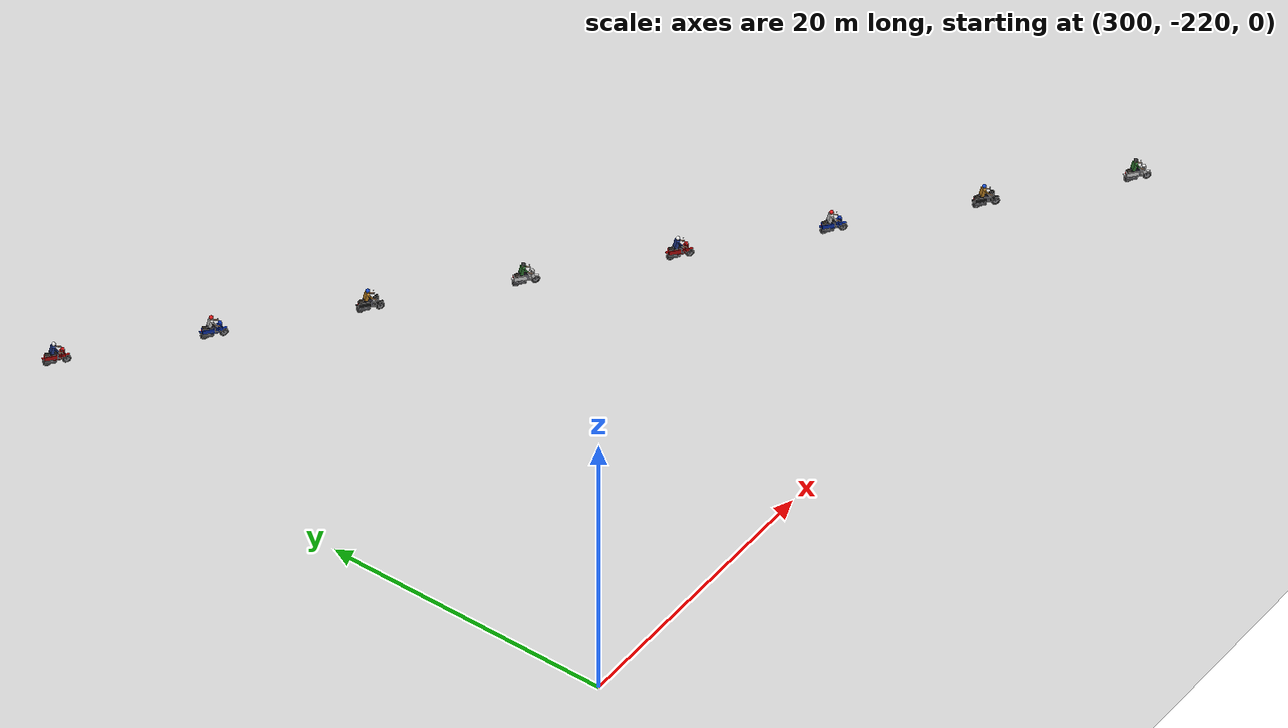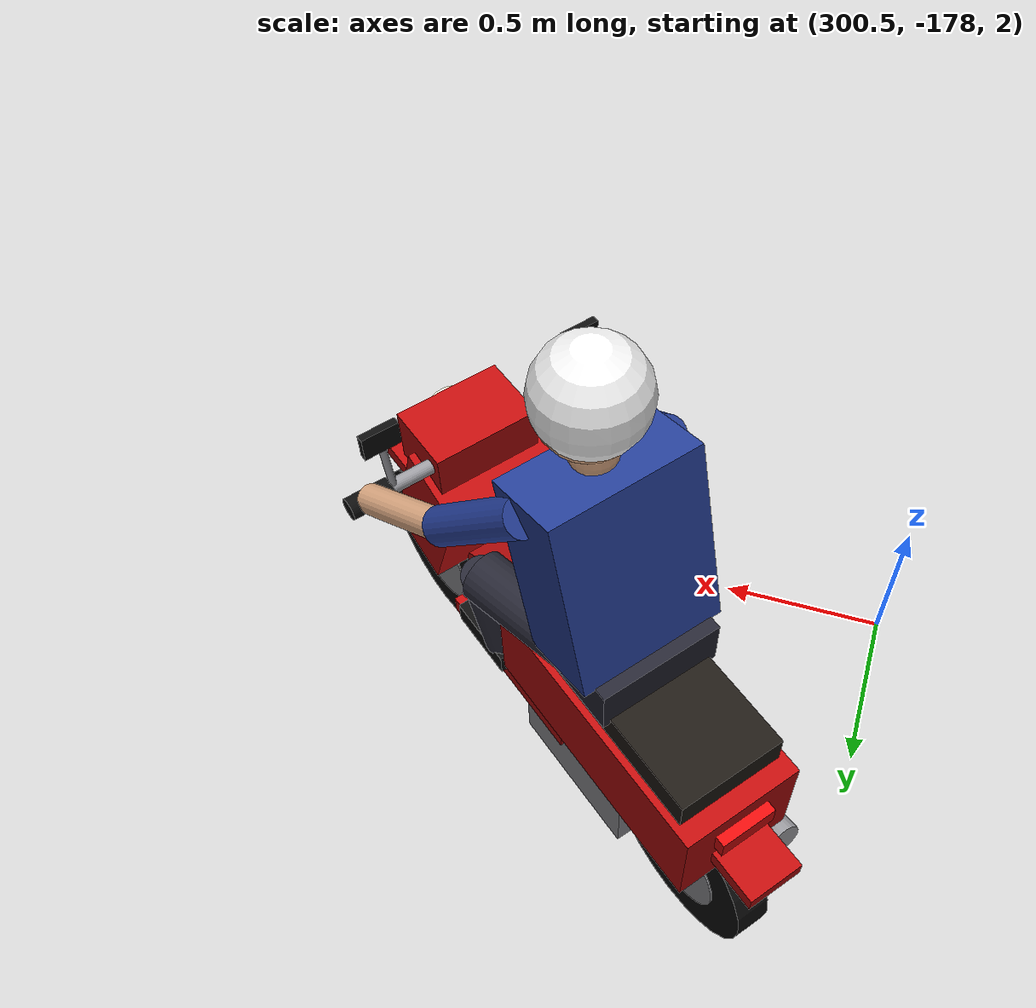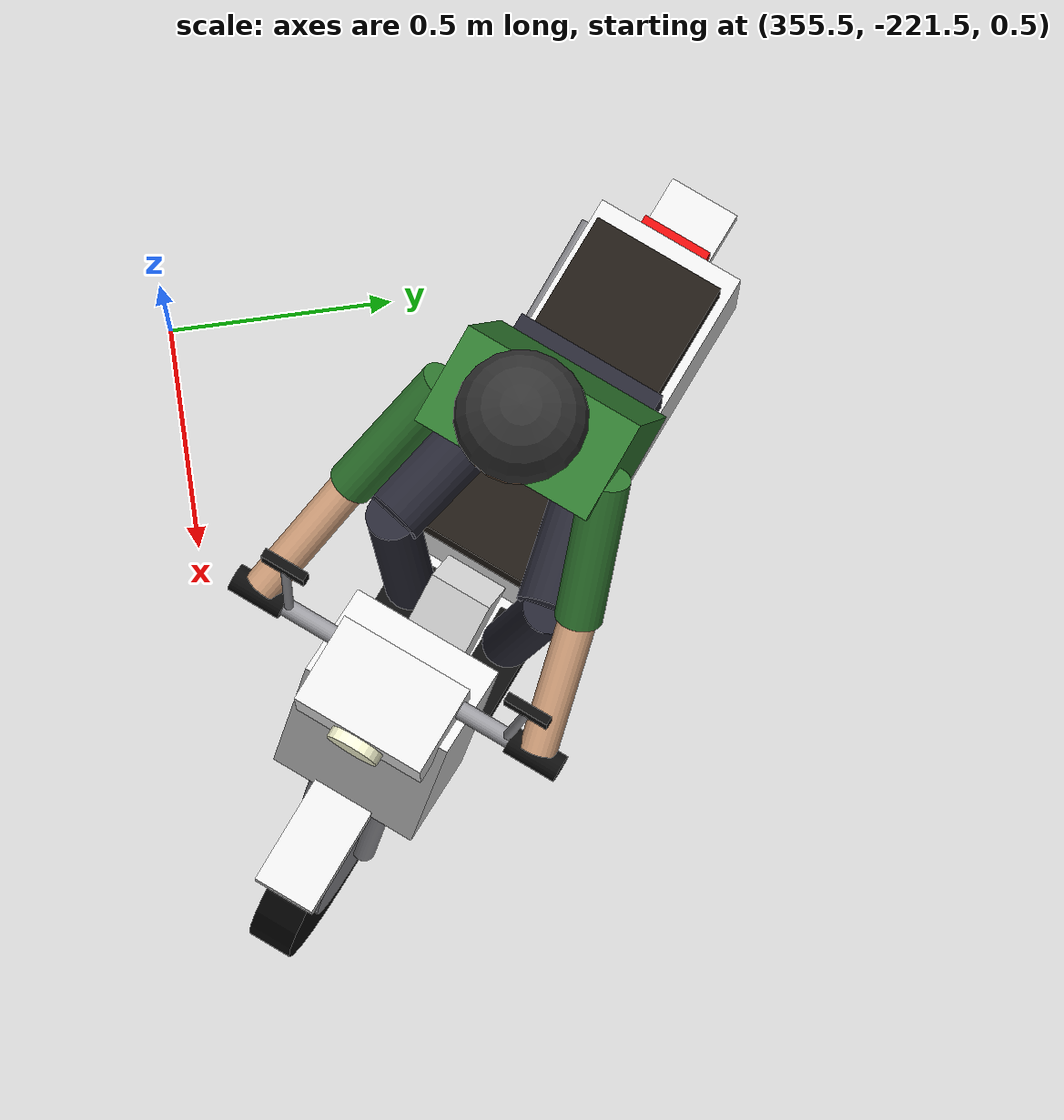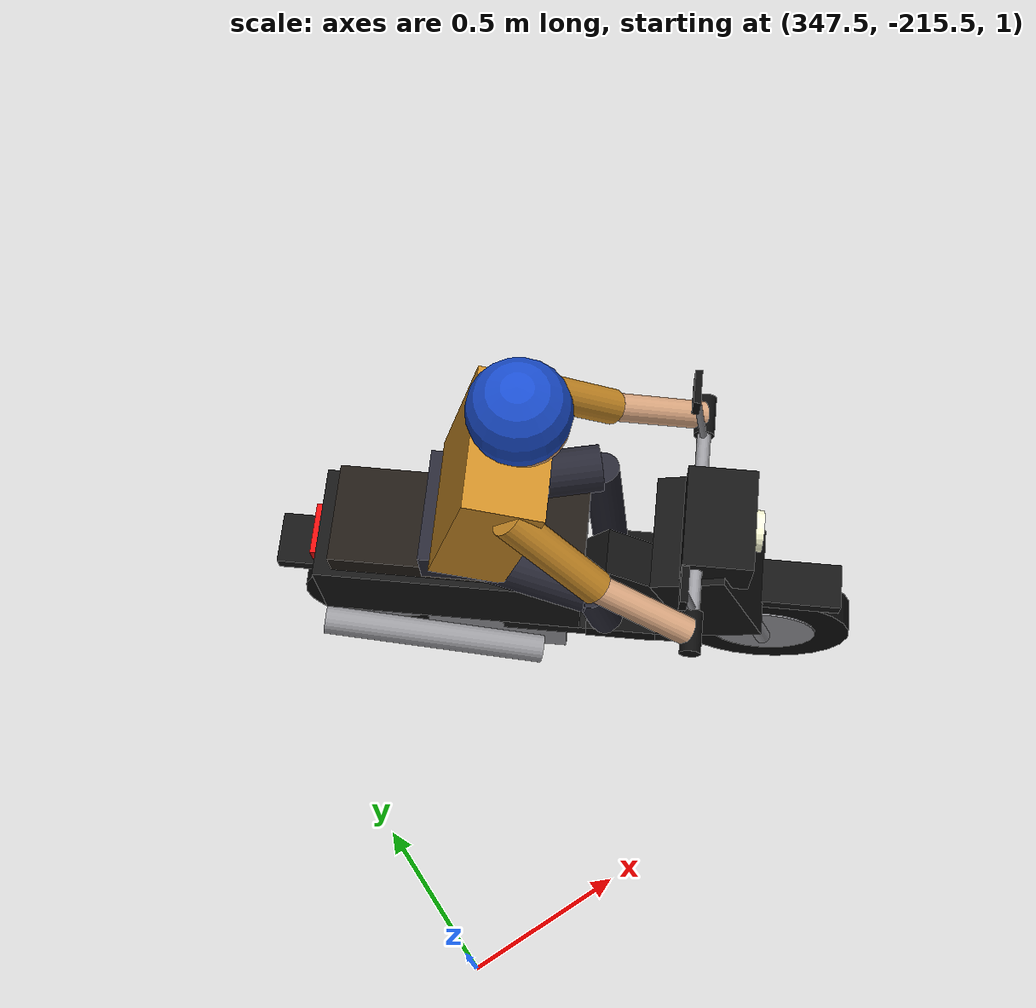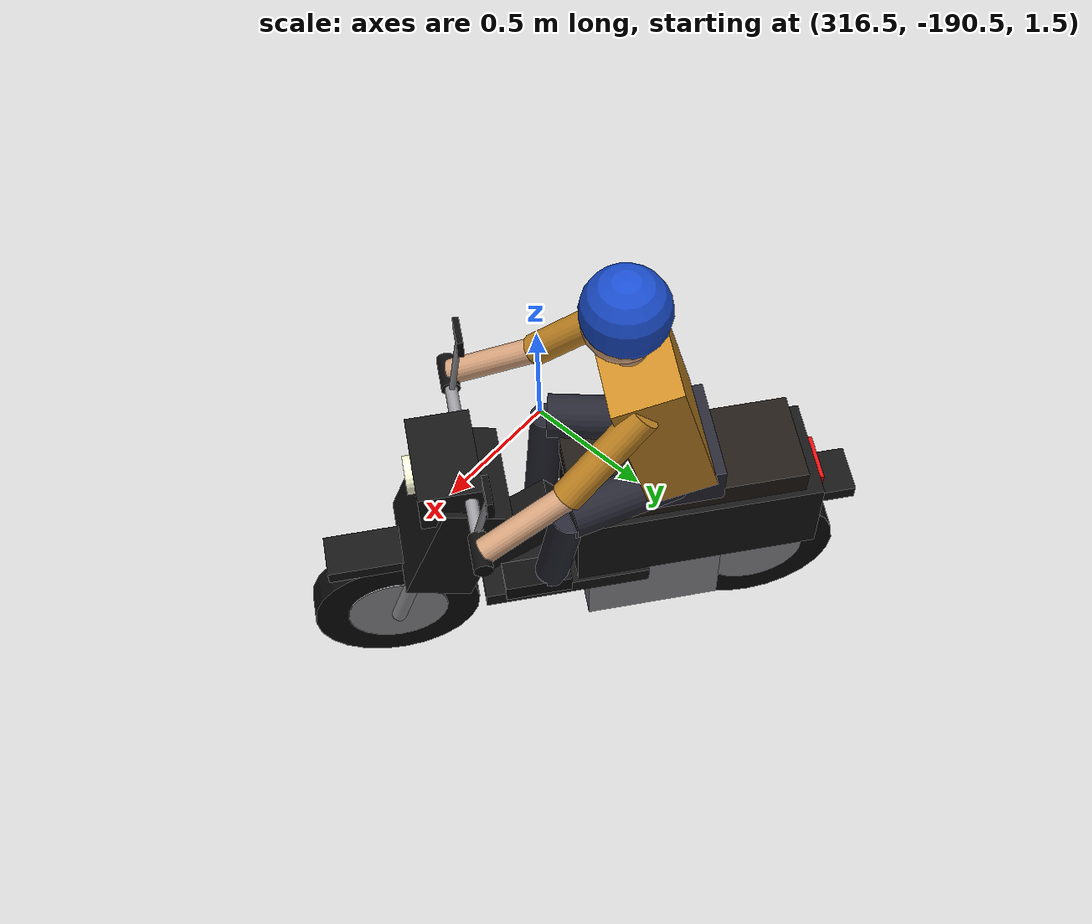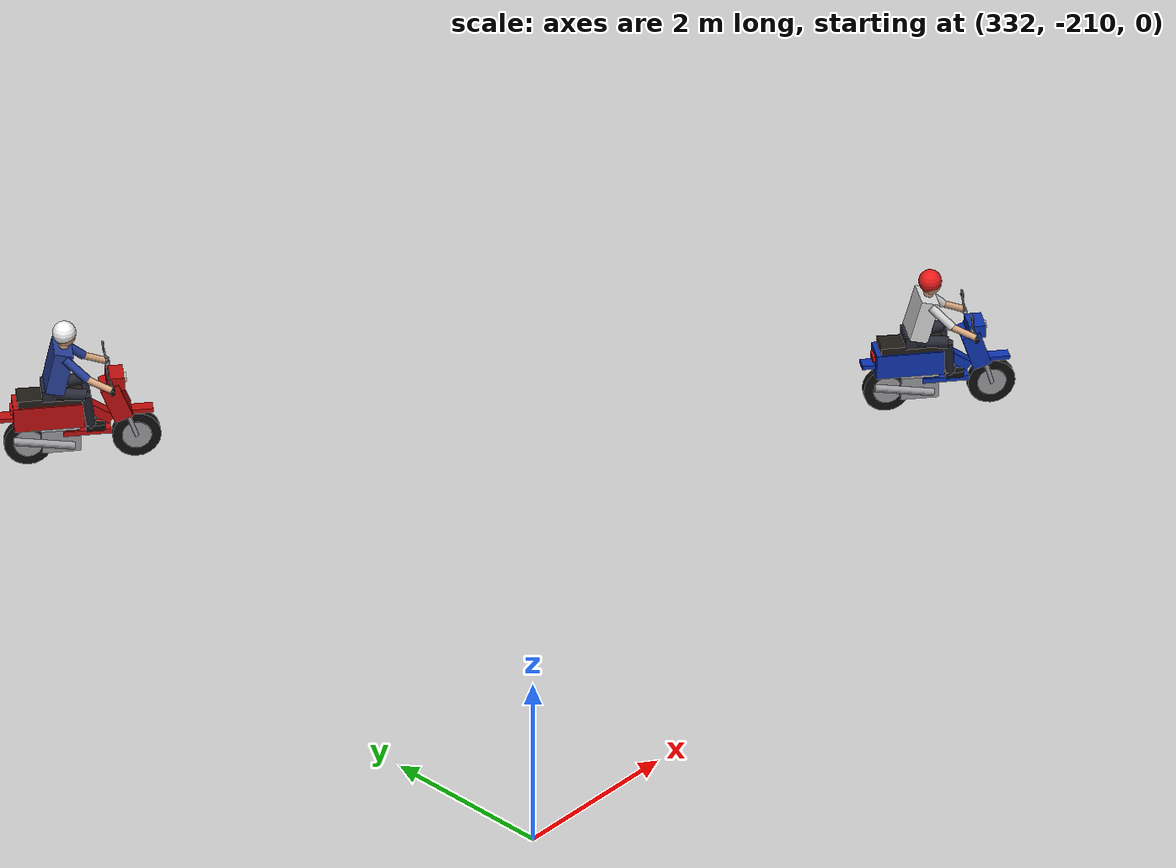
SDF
<sdf version="1.9">
 <world name="default">
  <physics type="ode">
   <max_step_size>0.004</max_step_size>
   <real_time_factor>1.0</real_time_factor>
   <real_time_update_rate>250</real_time_update_rate>
  </physics>
  <plugin name="gz::sim::systems::Physics" filename="gz-sim-physics-system"/>
  <plugin name="gz::sim::systems::UserCommands" filename="gz-sim-user-commands-system"/>
  <plugin name="gz::sim::systems::SceneBroadcaster" filename="gz-sim-scene-broadcaster-system"/>
  <plugin name="gz::sim::systems::Contact" filename="gz-sim-contact-system"/>
  <plugin name="gz::sim::systems::Imu" filename="gz-sim-imu-system"/>
  <plugin name="gz::sim::systems::AirPressure" filename="gz-sim-air-pressure-system"/>
  <plugin name="gz::sim::systems::Magnetometer" filename="gz-sim-magnetometer-system"/>
  <plugin name="gz::sim::systems::ApplyLinkWrench" filename="gz-sim-apply-link-wrench-system"/>
  <plugin name="gz::sim::systems::NavSat" filename="gz-sim-navsat-system"/>
  <plugin name="gz::sim::systems::Sensors" filename="gz-sim-sensors-system">
   <render_engine>ogre2</render_engine>
  </plugin>
  <gravity>0 0 -9.8</gravity>
  <magnetic_field>6e-06 2.3e-05 -4.2e-05</magnetic_field>
  <atmosphere type="adiabatic"/>
  <scene>
   <grid>false</grid>
   <ambient>0.4 0.4 0.4 1</ambient>
   <background>0.7 0.7 0.7 1</background>
   <shadows>true</shadows>
  </scene>
  <model name="ground_plane">
   <static>true</static>
   <link name="link">
    <collision name="collision">
     <geometry><plane><normal>0 0 1</normal><size>1 1</size></plane></geometry>
    </collision>
    <visual name="visual">
     <geometry><plane><normal>0 0 1</normal><size>100 100</size></plane></geometry>
     <material>
      <ambient>0.8 0.8 0.8 1</ambient>
      <diffuse>0.8 0.8 0.8 1</diffuse>
      <specular>0.8 0.8 0.8 1</specular>
     </material>
    </visual>
    <inertial>
     <mass>1</mass>
     <inertia><ixx>1</ixx><ixy>0</ixy><ixz>0</ixz><iyy>1</iyy><iyz>0</iyz><izz>1</izz></inertia>
    </inertial>
   </link>
  </model>
  <light name="sunUTC" type="directional">
   <pose>0 0 500 0 -0 0</pose>
   <intensity>1</intensity>
   <direction>0.001 0.625 -0.78</direction>
   <diffuse>0.904 0.904 0.904 1</diffuse>
   <specular>0.271 0.271 0.271 1</specular>
   <attenuation><range>2000</range><linear>0</linear><constant>1</constant><quadratic>0</quadratic></attenuation>
   <spot><inner_angle>0</inner_angle><outer_angle>0</outer_angle><falloff>0</falloff></spot>
  </light>
  <spherical_coordinates>
   <surface_model>EARTH_WGS84</surface_model>
   <world_frame_orientation>ENU</world_frame_orientation>
   <latitude_deg>47.397971057728974</latitude_deg>
   <longitude_deg>8.546163739800146</longitude_deg>
   <elevation>0</elevation>
  </spherical_coordinates>
  <include>
   <pose>301.40 -177.39 1.95 0 0 -0.67</pose>
   <uri>model://motorbike_red</uri>
   <name>motorbike_red_1</name>
  </include>
  <include>
   <pose>309.23 -183.61 1.75 0 0 -0.67</pose>
   <uri>model://motorbike_blue</uri>
   <name>motorbike_blue_1</name>
  </include>
  <include>
   <pose>317.07 -189.82 1.55 0 0 -0.67</pose>
   <uri>model://motorbike_black</uri>
   <name>motorbike_black_1</name>
  </include>
  <include>
   <pose>324.90 -196.04 1.36 0 0 -0.67</pose>
   <uri>model://motorbike_white</uri>
   <name>motorbike_white_1</name>
  </include>
  <include>
   <pose>332.74 -202.25 1.17 0 0 -0.67</pose>
   <uri>model://motorbike_red</uri>
   <name>motorbike_red_2</name>
  </include>
  <include>
   <pose>340.57 -208.46 0.97 0 0 -0.67</pose>
   <uri>model://motorbike_blue</uri>
   <name>motorbike_blue_2</name>
  </include>
  <include>
   <pose>348.41 -214.68 0.78 0 0 -0.67</pose>
   <uri>model://motorbike_black</uri>
   <name>motorbike_black_2</name>
  </include>
  <include>
   <pose>356.24 -220.89 0.60 0 0 -0.67</pose>
   <uri>model://motorbike_white</uri>
   <name>motorbike_white_2</name>
  </include>
 </world>
</sdf>

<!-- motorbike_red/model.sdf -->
<sdf version="1.6">
  <model name="motorbike_red">
    <static>true</static>
    <link name="link">
      <collision name="collision">
        <pose>0 0 0.5 0 0 0</pose>
        <geometry><box><size>1.8 0.7 1.0</size></box></geometry>
      </collision>
      <visual name="rear_tire">
        <pose>-0.6200 0.0000 0.2800 1.5708 0.0000 0.0000</pose>
        <geometry><cylinder><radius>0.28</radius><length>0.1</length></cylinder></geometry>
        <material><ambient>0.05 0.05 0.05 1</ambient><diffuse>0.05 0.05 0.05 1</diffuse><specular>0.2 0.2 0.2 1</specular></material>
      </visual>
      <visual name="rear_rim">
        <pose>-0.6200 0.0000 0.2800 1.5708 0.0000 0.0000</pose>
        <geometry><cylinder><radius>0.17</radius><length>0.11</length></cylinder></geometry>
        <material><ambient>0.6 0.6 0.62 1</ambient><diffuse>0.6 0.6 0.62 1</diffuse><specular>0.2 0.2 0.2 1</specular></material>
      </visual>
      <visual name="front_tire">
        <pose>0.6200 0.0000 0.2800 1.5708 0.0000 0.0000</pose>
        <geometry><cylinder><radius>0.28</radius><length>0.1</length></cylinder></geometry>
        <material><ambient>0.05 0.05 0.05 1</ambient><diffuse>0.05 0.05 0.05 1</diffuse><specular>0.2 0.2 0.2 1</specular></material>
      </visual>
      <visual name="front_rim">
        <pose>0.6200 0.0000 0.2800 1.5708 0.0000 0.0000</pose>
        <geometry><cylinder><radius>0.17</radius><length>0.11</length></cylinder></geometry>
        <material><ambient>0.6 0.6 0.62 1</ambient><diffuse>0.6 0.6 0.62 1</diffuse><specular>0.2 0.2 0.2 1</specular></material>
      </visual>
      <visual name="fork_l">
        <pose>0.5100 0.0700 0.6150 0.0000 0.3173 3.1416</pose>
        <geometry><cylinder><radius>0.025</radius><length>0.7051950084905593</length></cylinder></geometry>
        <material><ambient>0.6 0.6 0.62 1</ambient><diffuse>0.6 0.6 0.62 1</diffuse><specular>0.2 0.2 0.2 1</specular></material>
      </visual>
      <visual name="fork_r">
        <pose>0.5100 -0.0700 0.6150 0.0000 0.3173 3.1416</pose>
        <geometry><cylinder><radius>0.025</radius><length>0.7051950084905593</length></cylinder></geometry>
        <material><ambient>0.6 0.6 0.62 1</ambient><diffuse>0.6 0.6 0.62 1</diffuse><specular>0.2 0.2 0.2 1</specular></material>
      </visual>
      <visual name="front_fender">
        <pose>0.6200 0.0000 0.6000 0.0000 0.0000 0.0000</pose>
        <geometry><box><size>0.4 0.14 0.05</size></box></geometry>
        <material><ambient>0.75 0.05 0.05 1</ambient><diffuse>0.75 0.05 0.05 1</diffuse><specular>0.2 0.2 0.2 1</specular></material>
      </visual>
      <visual name="front_cowl">
        <pose>0.4000 0.0000 0.7800 0.0000 -0.3500 0.0000</pose>
        <geometry><box><size>0.22 0.34 0.45</size></box></geometry>
        <material><ambient>0.75 0.05 0.05 1</ambient><diffuse>0.75 0.05 0.05 1</diffuse><specular>0.2 0.2 0.2 1</specular></material>
      </visual>
      <visual name="headlight_housing">
        <pose>0.4000 0.0000 1.0300 0.0000 0.0000 0.0000</pose>
        <geometry><box><size>0.2 0.3 0.16</size></box></geometry>
        <material><ambient>0.75 0.05 0.05 1</ambient><diffuse>0.75 0.05 0.05 1</diffuse><specular>0.2 0.2 0.2 1</specular></material>
      </visual>
      <visual name="headlight">
        <pose>0.5100 0.0000 1.0300 0.0000 1.5708 0.0000</pose>
        <geometry><cylinder><radius>0.06</radius><length>0.03</length></cylinder></geometry>
        <material><ambient>1.0 1.0 0.85 1</ambient><diffuse>1.0 1.0 0.85 1</diffuse><specular>0.2 0.2 0.2 1</specular></material>
      </visual>
      <visual name="handlebar">
        <pose>0.3400 0.0000 1.0600 1.5708 0.0000 0.0000</pose>
        <geometry><cylinder><radius>0.02</radius><length>0.72</length></cylinder></geometry>
        <material><ambient>0.6 0.6 0.62 1</ambient><diffuse>0.6 0.6 0.62 1</diffuse><specular>0.2 0.2 0.2 1</specular></material>
      </visual>
      <visual name="grip_l">
        <pose>0.3400 0.3300 1.0600 1.5708 0.0000 0.0000</pose>
        <geometry><cylinder><radius>0.03</radius><length>0.12</length></cylinder></geometry>
        <material><ambient>0.05 0.05 0.05 1</ambient><diffuse>0.05 0.05 0.05 1</diffuse><specular>0.2 0.2 0.2 1</specular></material>
      </visual>
      <visual name="grip_r">
        <pose>0.3400 -0.3300 1.0600 1.5708 0.0000 0.0000</pose>
        <geometry><cylinder><radius>0.03</radius><length>0.12</length></cylinder></geometry>
        <material><ambient>0.05 0.05 0.05 1</ambient><diffuse>0.05 0.05 0.05 1</diffuse><specular>0.2 0.2 0.2 1</specular></material>
      </visual>
      <visual name="mirror_stem_l">
        <pose>0.3200 0.2730 1.1700 0.0000 0.2135 2.5652</pose>
        <geometry><cylinder><radius>0.01</radius><length>0.22511330480449174</length></cylinder></geometry>
        <material><ambient>0.6 0.6 0.62 1</ambient><diffuse>0.6 0.6 0.62 1</diffuse><specular>0.2 0.2 0.2 1</specular></material>
      </visual>
      <visual name="mirror_l">
        <pose>0.3000 0.2860 1.3000 0.0000 0.0000 0.0000</pose>
        <geometry><box><size>0.02 0.1 0.07</size></box></geometry>
        <material><ambient>0.05 0.05 0.05 1</ambient><diffuse>0.05 0.05 0.05 1</diffuse><specular>0.2 0.2 0.2 1</specular></material>
      </visual>
      <visual name="mirror_stem_r">
        <pose>0.3200 -0.2730 1.1700 0.0000 0.2135 -2.5652</pose>
        <geometry><cylinder><radius>0.01</radius><length>0.22511330480449174</length></cylinder></geometry>
        <material><ambient>0.6 0.6 0.62 1</ambient><diffuse>0.6 0.6 0.62 1</diffuse><specular>0.2 0.2 0.2 1</specular></material>
      </visual>
      <visual name="mirror_r">
        <pose>0.3000 -0.2860 1.3000 0.0000 0.0000 0.0000</pose>
        <geometry><box><size>0.02 0.1 0.07</size></box></geometry>
        <material><ambient>0.05 0.05 0.05 1</ambient><diffuse>0.05 0.05 0.05 1</diffuse><specular>0.2 0.2 0.2 1</specular></material>
      </visual>
      <visual name="floorboard">
        <pose>0.0500 0.0000 0.4200 0.0000 0.0000 0.0000</pose>
        <geometry><box><size>0.55 0.3 0.06</size></box></geometry>
        <material><ambient>0.75 0.05 0.05 1</ambient><diffuse>0.75 0.05 0.05 1</diffuse><specular>0.2 0.2 0.2 1</specular></material>
      </visual>
      <visual name="frame_tube">
        <pose>0.2000 0.0000 0.6200 0.0000 0.6000 0.0000</pose>
        <geometry><box><size>0.35 0.14 0.12</size></box></geometry>
        <material><ambient>0.75 0.05 0.05 1</ambient><diffuse>0.75 0.05 0.05 1</diffuse><specular>0.2 0.2 0.2 1</specular></material>
      </visual>
      <visual name="engine">
        <pose>-0.2500 0.0000 0.3200 0.0000 0.0000 0.0000</pose>
        <geometry><box><size>0.45 0.26 0.28</size></box></geometry>
        <material><ambient>0.6 0.6 0.62 1</ambient><diffuse>0.6 0.6 0.62 1</diffuse><specular>0.2 0.2 0.2 1</specular></material>
      </visual>
      <visual name="rear_body">
        <pose>-0.3800 0.0000 0.6600 0.0000 0.0000 0.0000</pose>
        <geometry><box><size>0.8 0.34 0.3</size></box></geometry>
        <material><ambient>0.75 0.05 0.05 1</ambient><diffuse>0.75 0.05 0.05 1</diffuse><specular>0.2 0.2 0.2 1</specular></material>
      </visual>
      <visual name="seat">
        <pose>-0.3500 0.0000 0.8550 0.0000 0.0000 0.0000</pose>
        <geometry><box><size>0.75 0.3 0.09</size></box></geometry>
        <material><ambient>0.12 0.1 0.08 1</ambient><diffuse>0.12 0.1 0.08 1</diffuse><specular>0.2 0.2 0.2 1</specular></material>
      </visual>
      <visual name="rear_fender">
        <pose>-0.7800 0.0000 0.6200 0.0000 0.0000 0.0000</pose>
        <geometry><box><size>0.3 0.16 0.05</size></box></geometry>
        <material><ambient>0.75 0.05 0.05 1</ambient><diffuse>0.75 0.05 0.05 1</diffuse><specular>0.2 0.2 0.2 1</specular></material>
      </visual>
      <visual name="taillight">
        <pose>-0.7900 0.0000 0.7200 0.0000 0.0000 0.0000</pose>
        <geometry><box><size>0.04 0.16 0.06</size></box></geometry>
        <material><ambient>0.9 0.05 0.05 1</ambient><diffuse>0.9 0.05 0.05 1</diffuse><specular>0.2 0.2 0.2 1</specular></material>
      </visual>
      <visual name="exhaust">
        <pose>-0.4500 -0.1800 0.3400 0.0000 1.4010 3.1416</pose>
        <geometry><cylinder><radius>0.045</radius><length>0.7102112361825882</length></cylinder></geometry>
        <material><ambient>0.6 0.6 0.62 1</ambient><diffuse>0.6 0.6 0.62 1</diffuse><specular>0.2 0.2 0.2 1</specular></material>
      </visual>
      <visual name="pelvis">
        <pose>-0.3200 0.0000 0.9500 0.0000 0.0000 0.0000</pose>
        <geometry><box><size>0.25 0.34 0.14</size></box></geometry>
        <material><ambient>0.15 0.15 0.2 1</ambient><diffuse>0.15 0.15 0.2 1</diffuse><specular>0.2 0.2 0.2 1</specular></material>
      </visual>
      <visual name="torso">
        <pose>-0.2400 0.0000 1.2400 0.0000 0.2500 0.0000</pose>
        <geometry><box><size>0.22 0.4 0.52</size></box></geometry>
        <material><ambient>0.15 0.25 0.6 1</ambient><diffuse>0.15 0.25 0.6 1</diffuse><specular>0.2 0.2 0.2 1</specular></material>
      </visual>
      <visual name="neck">
        <pose>-0.1600 0.0000 1.5200 0.0000 0.0000 0.0000</pose>
        <geometry><sphere><radius>0.06</radius></sphere></geometry>
        <material><ambient>0.85 0.65 0.5 1</ambient><diffuse>0.85 0.65 0.5 1</diffuse><specular>0.2 0.2 0.2 1</specular></material>
      </visual>
      <visual name="head">
        <pose>-0.1400 0.0000 1.6400 0.0000 0.0000 0.0000</pose>
        <geometry><sphere><radius>0.12</radius></sphere></geometry>
        <material><ambient>0.85 0.65 0.5 1</ambient><diffuse>0.85 0.65 0.5 1</diffuse><specular>0.2 0.2 0.2 1</specular></material>
      </visual>
      <visual name="helmet">
        <pose>-0.1500 0.0000 1.6800 0.0000 0.0000 0.0000</pose>
        <geometry><sphere><radius>0.135</radius></sphere></geometry>
        <material><ambient>0.95 0.95 0.95 1</ambient><diffuse>0.95 0.95 0.95 1</diffuse><specular>0.2 0.2 0.2 1</specular></material>
      </visual>
      <visual name="upper_arm_l">
        <pose>-0.0500 0.2300 1.3200 0.0000 2.3299 0.3218</pose>
        <geometry><cylinder><radius>0.05</radius><length>0.3487119154832539</length></cylinder></geometry>
        <material><ambient>0.15 0.25 0.6 1</ambient><diffuse>0.15 0.25 0.6 1</diffuse><specular>0.2 0.2 0.2 1</specular></material>
      </visual>
      <visual name="forearm_l">
        <pose>0.2000 0.3000 1.1350 0.0000 2.0241 0.2268</pose>
        <geometry><cylinder><radius>0.04</radius><length>0.2968164415931166</length></cylinder></geometry>
        <material><ambient>0.85 0.65 0.5 1</ambient><diffuse>0.85 0.65 0.5 1</diffuse><specular>0.2 0.2 0.2 1</specular></material>
      </visual>
      <visual name="thigh_l">
        <pose>-0.1250 0.1500 0.9500 0.0000 1.5708 0.2247</pose>
        <geometry><cylinder><radius>0.07</radius><length>0.3590264614203248</length></cylinder></geometry>
        <material><ambient>0.15 0.15 0.2 1</ambient><diffuse>0.15 0.15 0.2 1</diffuse><specular>0.2 0.2 0.2 1</specular></material>
      </visual>
      <visual name="shin_l">
        <pose>0.0750 0.1550 0.7250 0.0000 2.9527 -0.9505</pose>
        <geometry><cylinder><radius>0.055</radius><length>0.4581484475582122</length></cylinder></geometry>
        <material><ambient>0.15 0.15 0.2 1</ambient><diffuse>0.15 0.15 0.2 1</diffuse><specular>0.2 0.2 0.2 1</specular></material>
      </visual>
      <visual name="shoe_l">
        <pose>0.1500 0.1200 0.4800 0.0000 0.0000 0.0000</pose>
        <geometry><box><size>0.22 0.1 0.07</size></box></geometry>
        <material><ambient>0.05 0.05 0.05 1</ambient><diffuse>0.05 0.05 0.05 1</diffuse><specular>0.2 0.2 0.2 1</specular></material>
      </visual>
      <visual name="upper_arm_r">
        <pose>-0.0500 -0.2300 1.3200 0.0000 2.3299 -0.3218</pose>
        <geometry><cylinder><radius>0.05</radius><length>0.3487119154832539</length></cylinder></geometry>
        <material><ambient>0.15 0.25 0.6 1</ambient><diffuse>0.15 0.25 0.6 1</diffuse><specular>0.2 0.2 0.2 1</specular></material>
      </visual>
      <visual name="forearm_r">
        <pose>0.2000 -0.3000 1.1350 0.0000 2.0241 -0.2268</pose>
        <geometry><cylinder><radius>0.04</radius><length>0.2968164415931166</length></cylinder></geometry>
        <material><ambient>0.85 0.65 0.5 1</ambient><diffuse>0.85 0.65 0.5 1</diffuse><specular>0.2 0.2 0.2 1</specular></material>
      </visual>
      <visual name="thigh_r">
        <pose>-0.1250 -0.1500 0.9500 0.0000 1.5708 -0.2247</pose>
        <geometry><cylinder><radius>0.07</radius><length>0.3590264614203248</length></cylinder></geometry>
        <material><ambient>0.15 0.15 0.2 1</ambient><diffuse>0.15 0.15 0.2 1</diffuse><specular>0.2 0.2 0.2 1</specular></material>
      </visual>
      <visual name="shin_r">
        <pose>0.0750 -0.1550 0.7250 0.0000 2.9527 0.9505</pose>
        <geometry><cylinder><radius>0.055</radius><length>0.4581484475582122</length></cylinder></geometry>
        <material><ambient>0.15 0.15 0.2 1</ambient><diffuse>0.15 0.15 0.2 1</diffuse><specular>0.2 0.2 0.2 1</specular></material>
      </visual>
      <visual name="shoe_r">
        <pose>0.1500 -0.1200 0.4800 0.0000 0.0000 0.0000</pose>
        <geometry><box><size>0.22 0.1 0.07</size></box></geometry>
        <material><ambient>0.05 0.05 0.05 1</ambient><diffuse>0.05 0.05 0.05 1</diffuse><specular>0.2 0.2 0.2 1</specular></material>
      </visual>
    </link>
  </model>
</sdf>

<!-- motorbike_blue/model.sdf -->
<sdf version="1.6">
  <model name="motorbike_blue">
    <static>true</static>
    <link name="link">
      <collision name="collision">
        <pose>0 0 0.5 0 0 0</pose>
        <geometry><box><size>1.8 0.7 1.0</size></box></geometry>
      </collision>
      <visual name="rear_tire">
        <pose>-0.6200 0.0000 0.2800 1.5708 0.0000 0.0000</pose>
        <geometry><cylinder><radius>0.28</radius><length>0.1</length></cylinder></geometry>
        <material><ambient>0.05 0.05 0.05 1</ambient><diffuse>0.05 0.05 0.05 1</diffuse><specular>0.2 0.2 0.2 1</specular></material>
      </visual>
      <visual name="rear_rim">
        <pose>-0.6200 0.0000 0.2800 1.5708 0.0000 0.0000</pose>
        <geometry><cylinder><radius>0.17</radius><length>0.11</length></cylinder></geometry>
        <material><ambient>0.6 0.6 0.62 1</ambient><diffuse>0.6 0.6 0.62 1</diffuse><specular>0.2 0.2 0.2 1</specular></material>
      </visual>
      <visual name="front_tire">
        <pose>0.6200 0.0000 0.2800 1.5708 0.0000 0.0000</pose>
        <geometry><cylinder><radius>0.28</radius><length>0.1</length></cylinder></geometry>
        <material><ambient>0.05 0.05 0.05 1</ambient><diffuse>0.05 0.05 0.05 1</diffuse><specular>0.2 0.2 0.2 1</specular></material>
      </visual>
      <visual name="front_rim">
        <pose>0.6200 0.0000 0.2800 1.5708 0.0000 0.0000</pose>
        <geometry><cylinder><radius>0.17</radius><length>0.11</length></cylinder></geometry>
        <material><ambient>0.6 0.6 0.62 1</ambient><diffuse>0.6 0.6 0.62 1</diffuse><specular>0.2 0.2 0.2 1</specular></material>
      </visual>
      <visual name="fork_l">
        <pose>0.5100 0.0700 0.6150 0.0000 0.3173 3.1416</pose>
        <geometry><cylinder><radius>0.025</radius><length>0.7051950084905593</length></cylinder></geometry>
        <material><ambient>0.6 0.6 0.62 1</ambient><diffuse>0.6 0.6 0.62 1</diffuse><specular>0.2 0.2 0.2 1</specular></material>
      </visual>
      <visual name="fork_r">
        <pose>0.5100 -0.0700 0.6150 0.0000 0.3173 3.1416</pose>
        <geometry><cylinder><radius>0.025</radius><length>0.7051950084905593</length></cylinder></geometry>
        <material><ambient>0.6 0.6 0.62 1</ambient><diffuse>0.6 0.6 0.62 1</diffuse><specular>0.2 0.2 0.2 1</specular></material>
      </visual>
      <visual name="front_fender">
        <pose>0.6200 0.0000 0.6000 0.0000 0.0000 0.0000</pose>
        <geometry><box><size>0.4 0.14 0.05</size></box></geometry>
        <material><ambient>0.05 0.2 0.7 1</ambient><diffuse>0.05 0.2 0.7 1</diffuse><specular>0.2 0.2 0.2 1</specular></material>
      </visual>
      <visual name="front_cowl">
        <pose>0.4000 0.0000 0.7800 0.0000 -0.3500 0.0000</pose>
        <geometry><box><size>0.22 0.34 0.45</size></box></geometry>
        <material><ambient>0.05 0.2 0.7 1</ambient><diffuse>0.05 0.2 0.7 1</diffuse><specular>0.2 0.2 0.2 1</specular></material>
      </visual>
      <visual name="headlight_housing">
        <pose>0.4000 0.0000 1.0300 0.0000 0.0000 0.0000</pose>
        <geometry><box><size>0.2 0.3 0.16</size></box></geometry>
        <material><ambient>0.05 0.2 0.7 1</ambient><diffuse>0.05 0.2 0.7 1</diffuse><specular>0.2 0.2 0.2 1</specular></material>
      </visual>
      <visual name="headlight">
        <pose>0.5100 0.0000 1.0300 0.0000 1.5708 0.0000</pose>
        <geometry><cylinder><radius>0.06</radius><length>0.03</length></cylinder></geometry>
        <material><ambient>1.0 1.0 0.85 1</ambient><diffuse>1.0 1.0 0.85 1</diffuse><specular>0.2 0.2 0.2 1</specular></material>
      </visual>
      <visual name="handlebar">
        <pose>0.3400 0.0000 1.0600 1.5708 0.0000 0.0000</pose>
        <geometry><cylinder><radius>0.02</radius><length>0.72</length></cylinder></geometry>
        <material><ambient>0.6 0.6 0.62 1</ambient><diffuse>0.6 0.6 0.62 1</diffuse><specular>0.2 0.2 0.2 1</specular></material>
      </visual>
      <visual name="grip_l">
        <pose>0.3400 0.3300 1.0600 1.5708 0.0000 0.0000</pose>
        <geometry><cylinder><radius>0.03</radius><length>0.12</length></cylinder></geometry>
        <material><ambient>0.05 0.05 0.05 1</ambient><diffuse>0.05 0.05 0.05 1</diffuse><specular>0.2 0.2 0.2 1</specular></material>
      </visual>
      <visual name="grip_r">
        <pose>0.3400 -0.3300 1.0600 1.5708 0.0000 0.0000</pose>
        <geometry><cylinder><radius>0.03</radius><length>0.12</length></cylinder></geometry>
        <material><ambient>0.05 0.05 0.05 1</ambient><diffuse>0.05 0.05 0.05 1</diffuse><specular>0.2 0.2 0.2 1</specular></material>
      </visual>
      <visual name="mirror_stem_l">
        <pose>0.3200 0.2730 1.1700 0.0000 0.2135 2.5652</pose>
        <geometry><cylinder><radius>0.01</radius><length>0.22511330480449174</length></cylinder></geometry>
        <material><ambient>0.6 0.6 0.62 1</ambient><diffuse>0.6 0.6 0.62 1</diffuse><specular>0.2 0.2 0.2 1</specular></material>
      </visual>
      <visual name="mirror_l">
        <pose>0.3000 0.2860 1.3000 0.0000 0.0000 0.0000</pose>
        <geometry><box><size>0.02 0.1 0.07</size></box></geometry>
        <material><ambient>0.05 0.05 0.05 1</ambient><diffuse>0.05 0.05 0.05 1</diffuse><specular>0.2 0.2 0.2 1</specular></material>
      </visual>
      <visual name="mirror_stem_r">
        <pose>0.3200 -0.2730 1.1700 0.0000 0.2135 -2.5652</pose>
        <geometry><cylinder><radius>0.01</radius><length>0.22511330480449174</length></cylinder></geometry>
        <material><ambient>0.6 0.6 0.62 1</ambient><diffuse>0.6 0.6 0.62 1</diffuse><specular>0.2 0.2 0.2 1</specular></material>
      </visual>
      <visual name="mirror_r">
        <pose>0.3000 -0.2860 1.3000 0.0000 0.0000 0.0000</pose>
        <geometry><box><size>0.02 0.1 0.07</size></box></geometry>
        <material><ambient>0.05 0.05 0.05 1</ambient><diffuse>0.05 0.05 0.05 1</diffuse><specular>0.2 0.2 0.2 1</specular></material>
      </visual>
      <visual name="floorboard">
        <pose>0.0500 0.0000 0.4200 0.0000 0.0000 0.0000</pose>
        <geometry><box><size>0.55 0.3 0.06</size></box></geometry>
        <material><ambient>0.05 0.2 0.7 1</ambient><diffuse>0.05 0.2 0.7 1</diffuse><specular>0.2 0.2 0.2 1</specular></material>
      </visual>
      <visual name="frame_tube">
        <pose>0.2000 0.0000 0.6200 0.0000 0.6000 0.0000</pose>
        <geometry><box><size>0.35 0.14 0.12</size></box></geometry>
        <material><ambient>0.05 0.2 0.7 1</ambient><diffuse>0.05 0.2 0.7 1</diffuse><specular>0.2 0.2 0.2 1</specular></material>
      </visual>
      <visual name="engine">
        <pose>-0.2500 0.0000 0.3200 0.0000 0.0000 0.0000</pose>
        <geometry><box><size>0.45 0.26 0.28</size></box></geometry>
        <material><ambient>0.6 0.6 0.62 1</ambient><diffuse>0.6 0.6 0.62 1</diffuse><specular>0.2 0.2 0.2 1</specular></material>
      </visual>
      <visual name="rear_body">
        <pose>-0.3800 0.0000 0.6600 0.0000 0.0000 0.0000</pose>
        <geometry><box><size>0.8 0.34 0.3</size></box></geometry>
        <material><ambient>0.05 0.2 0.7 1</ambient><diffuse>0.05 0.2 0.7 1</diffuse><specular>0.2 0.2 0.2 1</specular></material>
      </visual>
      <visual name="seat">
        <pose>-0.3500 0.0000 0.8550 0.0000 0.0000 0.0000</pose>
        <geometry><box><size>0.75 0.3 0.09</size></box></geometry>
        <material><ambient>0.12 0.1 0.08 1</ambient><diffuse>0.12 0.1 0.08 1</diffuse><specular>0.2 0.2 0.2 1</specular></material>
      </visual>
      <visual name="rear_fender">
        <pose>-0.7800 0.0000 0.6200 0.0000 0.0000 0.0000</pose>
        <geometry><box><size>0.3 0.16 0.05</size></box></geometry>
        <material><ambient>0.05 0.2 0.7 1</ambient><diffuse>0.05 0.2 0.7 1</diffuse><specular>0.2 0.2 0.2 1</specular></material>
      </visual>
      <visual name="taillight">
        <pose>-0.7900 0.0000 0.7200 0.0000 0.0000 0.0000</pose>
        <geometry><box><size>0.04 0.16 0.06</size></box></geometry>
        <material><ambient>0.9 0.05 0.05 1</ambient><diffuse>0.9 0.05 0.05 1</diffuse><specular>0.2 0.2 0.2 1</specular></material>
      </visual>
      <visual name="exhaust">
        <pose>-0.4500 -0.1800 0.3400 0.0000 1.4010 3.1416</pose>
        <geometry><cylinder><radius>0.045</radius><length>0.7102112361825882</length></cylinder></geometry>
        <material><ambient>0.6 0.6 0.62 1</ambient><diffuse>0.6 0.6 0.62 1</diffuse><specular>0.2 0.2 0.2 1</specular></material>
      </visual>
      <visual name="pelvis">
        <pose>-0.3200 0.0000 0.9500 0.0000 0.0000 0.0000</pose>
        <geometry><box><size>0.25 0.34 0.14</size></box></geometry>
        <material><ambient>0.15 0.15 0.2 1</ambient><diffuse>0.15 0.15 0.2 1</diffuse><specular>0.2 0.2 0.2 1</specular></material>
      </visual>
      <visual name="torso">
        <pose>-0.2400 0.0000 1.2400 0.0000 0.2500 0.0000</pose>
        <geometry><box><size>0.22 0.4 0.52</size></box></geometry>
        <material><ambient>0.85 0.85 0.85 1</ambient><diffuse>0.85 0.85 0.85 1</diffuse><specular>0.2 0.2 0.2 1</specular></material>
      </visual>
      <visual name="neck">
        <pose>-0.1600 0.0000 1.5200 0.0000 0.0000 0.0000</pose>
        <geometry><sphere><radius>0.06</radius></sphere></geometry>
        <material><ambient>0.85 0.65 0.5 1</ambient><diffuse>0.85 0.65 0.5 1</diffuse><specular>0.2 0.2 0.2 1</specular></material>
      </visual>
      <visual name="head">
        <pose>-0.1400 0.0000 1.6400 0.0000 0.0000 0.0000</pose>
        <geometry><sphere><radius>0.12</radius></sphere></geometry>
        <material><ambient>0.85 0.65 0.5 1</ambient><diffuse>0.85 0.65 0.5 1</diffuse><specular>0.2 0.2 0.2 1</specular></material>
      </visual>
      <visual name="helmet">
        <pose>-0.1500 0.0000 1.6800 0.0000 0.0000 0.0000</pose>
        <geometry><sphere><radius>0.135</radius></sphere></geometry>
        <material><ambient>0.9 0.1 0.1 1</ambient><diffuse>0.9 0.1 0.1 1</diffuse><specular>0.2 0.2 0.2 1</specular></material>
      </visual>
      <visual name="upper_arm_l">
        <pose>-0.0500 0.2300 1.3200 0.0000 2.3299 0.3218</pose>
        <geometry><cylinder><radius>0.05</radius><length>0.3487119154832539</length></cylinder></geometry>
        <material><ambient>0.85 0.85 0.85 1</ambient><diffuse>0.85 0.85 0.85 1</diffuse><specular>0.2 0.2 0.2 1</specular></material>
      </visual>
      <visual name="forearm_l">
        <pose>0.2000 0.3000 1.1350 0.0000 2.0241 0.2268</pose>
        <geometry><cylinder><radius>0.04</radius><length>0.2968164415931166</length></cylinder></geometry>
        <material><ambient>0.85 0.65 0.5 1</ambient><diffuse>0.85 0.65 0.5 1</diffuse><specular>0.2 0.2 0.2 1</specular></material>
      </visual>
      <visual name="thigh_l">
        <pose>-0.1250 0.1500 0.9500 0.0000 1.5708 0.2247</pose>
        <geometry><cylinder><radius>0.07</radius><length>0.3590264614203248</length></cylinder></geometry>
        <material><ambient>0.15 0.15 0.2 1</ambient><diffuse>0.15 0.15 0.2 1</diffuse><specular>0.2 0.2 0.2 1</specular></material>
      </visual>
      <visual name="shin_l">
        <pose>0.0750 0.1550 0.7250 0.0000 2.9527 -0.9505</pose>
        <geometry><cylinder><radius>0.055</radius><length>0.4581484475582122</length></cylinder></geometry>
        <material><ambient>0.15 0.15 0.2 1</ambient><diffuse>0.15 0.15 0.2 1</diffuse><specular>0.2 0.2 0.2 1</specular></material>
      </visual>
      <visual name="shoe_l">
        <pose>0.1500 0.1200 0.4800 0.0000 0.0000 0.0000</pose>
        <geometry><box><size>0.22 0.1 0.07</size></box></geometry>
        <material><ambient>0.05 0.05 0.05 1</ambient><diffuse>0.05 0.05 0.05 1</diffuse><specular>0.2 0.2 0.2 1</specular></material>
      </visual>
      <visual name="upper_arm_r">
        <pose>-0.0500 -0.2300 1.3200 0.0000 2.3299 -0.3218</pose>
        <geometry><cylinder><radius>0.05</radius><length>0.3487119154832539</length></cylinder></geometry>
        <material><ambient>0.85 0.85 0.85 1</ambient><diffuse>0.85 0.85 0.85 1</diffuse><specular>0.2 0.2 0.2 1</specular></material>
      </visual>
      <visual name="forearm_r">
        <pose>0.2000 -0.3000 1.1350 0.0000 2.0241 -0.2268</pose>
        <geometry><cylinder><radius>0.04</radius><length>0.2968164415931166</length></cylinder></geometry>
        <material><ambient>0.85 0.65 0.5 1</ambient><diffuse>0.85 0.65 0.5 1</diffuse><specular>0.2 0.2 0.2 1</specular></material>
      </visual>
      <visual name="thigh_r">
        <pose>-0.1250 -0.1500 0.9500 0.0000 1.5708 -0.2247</pose>
        <geometry><cylinder><radius>0.07</radius><length>0.3590264614203248</length></cylinder></geometry>
        <material><ambient>0.15 0.15 0.2 1</ambient><diffuse>0.15 0.15 0.2 1</diffuse><specular>0.2 0.2 0.2 1</specular></material>
      </visual>
      <visual name="shin_r">
        <pose>0.0750 -0.1550 0.7250 0.0000 2.9527 0.9505</pose>
        <geometry><cylinder><radius>0.055</radius><length>0.4581484475582122</length></cylinder></geometry>
        <material><ambient>0.15 0.15 0.2 1</ambient><diffuse>0.15 0.15 0.2 1</diffuse><specular>0.2 0.2 0.2 1</specular></material>
      </visual>
      <visual name="shoe_r">
        <pose>0.1500 -0.1200 0.4800 0.0000 0.0000 0.0000</pose>
        <geometry><box><size>0.22 0.1 0.07</size></box></geometry>
        <material><ambient>0.05 0.05 0.05 1</ambient><diffuse>0.05 0.05 0.05 1</diffuse><specular>0.2 0.2 0.2 1</specular></material>
      </visual>
    </link>
  </model>
</sdf>

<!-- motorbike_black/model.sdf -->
<sdf version="1.6">
  <model name="motorbike_black">
    <static>true</static>
    <link name="link">
      <collision name="collision">
        <pose>0 0 0.5 0 0 0</pose>
        <geometry><box><size>1.8 0.7 1.0</size></box></geometry>
      </collision>
      <visual name="rear_tire">
        <pose>-0.6200 0.0000 0.2800 1.5708 0.0000 0.0000</pose>
        <geometry><cylinder><radius>0.28</radius><length>0.1</length></cylinder></geometry>
        <material><ambient>0.05 0.05 0.05 1</ambient><diffuse>0.05 0.05 0.05 1</diffuse><specular>0.2 0.2 0.2 1</specular></material>
      </visual>
      <visual name="rear_rim">
        <pose>-0.6200 0.0000 0.2800 1.5708 0.0000 0.0000</pose>
        <geometry><cylinder><radius>0.17</radius><length>0.11</length></cylinder></geometry>
        <material><ambient>0.6 0.6 0.62 1</ambient><diffuse>0.6 0.6 0.62 1</diffuse><specular>0.2 0.2 0.2 1</specular></material>
      </visual>
      <visual name="front_tire">
        <pose>0.6200 0.0000 0.2800 1.5708 0.0000 0.0000</pose>
        <geometry><cylinder><radius>0.28</radius><length>0.1</length></cylinder></geometry>
        <material><ambient>0.05 0.05 0.05 1</ambient><diffuse>0.05 0.05 0.05 1</diffuse><specular>0.2 0.2 0.2 1</specular></material>
      </visual>
      <visual name="front_rim">
        <pose>0.6200 0.0000 0.2800 1.5708 0.0000 0.0000</pose>
        <geometry><cylinder><radius>0.17</radius><length>0.11</length></cylinder></geometry>
        <material><ambient>0.6 0.6 0.62 1</ambient><diffuse>0.6 0.6 0.62 1</diffuse><specular>0.2 0.2 0.2 1</specular></material>
      </visual>
      <visual name="fork_l">
        <pose>0.5100 0.0700 0.6150 0.0000 0.3173 3.1416</pose>
        <geometry><cylinder><radius>0.025</radius><length>0.7051950084905593</length></cylinder></geometry>
        <material><ambient>0.6 0.6 0.62 1</ambient><diffuse>0.6 0.6 0.62 1</diffuse><specular>0.2 0.2 0.2 1</specular></material>
      </visual>
      <visual name="fork_r">
        <pose>0.5100 -0.0700 0.6150 0.0000 0.3173 3.1416</pose>
        <geometry><cylinder><radius>0.025</radius><length>0.7051950084905593</length></cylinder></geometry>
        <material><ambient>0.6 0.6 0.62 1</ambient><diffuse>0.6 0.6 0.62 1</diffuse><specular>0.2 0.2 0.2 1</specular></material>
      </visual>
      <visual name="front_fender">
        <pose>0.6200 0.0000 0.6000 0.0000 0.0000 0.0000</pose>
        <geometry><box><size>0.4 0.14 0.05</size></box></geometry>
        <material><ambient>0.08 0.08 0.08 1</ambient><diffuse>0.08 0.08 0.08 1</diffuse><specular>0.2 0.2 0.2 1</specular></material>
      </visual>
      <visual name="front_cowl">
        <pose>0.4000 0.0000 0.7800 0.0000 -0.3500 0.0000</pose>
        <geometry><box><size>0.22 0.34 0.45</size></box></geometry>
        <material><ambient>0.08 0.08 0.08 1</ambient><diffuse>0.08 0.08 0.08 1</diffuse><specular>0.2 0.2 0.2 1</specular></material>
      </visual>
      <visual name="headlight_housing">
        <pose>0.4000 0.0000 1.0300 0.0000 0.0000 0.0000</pose>
        <geometry><box><size>0.2 0.3 0.16</size></box></geometry>
        <material><ambient>0.08 0.08 0.08 1</ambient><diffuse>0.08 0.08 0.08 1</diffuse><specular>0.2 0.2 0.2 1</specular></material>
      </visual>
      <visual name="headlight">
        <pose>0.5100 0.0000 1.0300 0.0000 1.5708 0.0000</pose>
        <geometry><cylinder><radius>0.06</radius><length>0.03</length></cylinder></geometry>
        <material><ambient>1.0 1.0 0.85 1</ambient><diffuse>1.0 1.0 0.85 1</diffuse><specular>0.2 0.2 0.2 1</specular></material>
      </visual>
      <visual name="handlebar">
        <pose>0.3400 0.0000 1.0600 1.5708 0.0000 0.0000</pose>
        <geometry><cylinder><radius>0.02</radius><length>0.72</length></cylinder></geometry>
        <material><ambient>0.6 0.6 0.62 1</ambient><diffuse>0.6 0.6 0.62 1</diffuse><specular>0.2 0.2 0.2 1</specular></material>
      </visual>
      <visual name="grip_l">
        <pose>0.3400 0.3300 1.0600 1.5708 0.0000 0.0000</pose>
        <geometry><cylinder><radius>0.03</radius><length>0.12</length></cylinder></geometry>
        <material><ambient>0.05 0.05 0.05 1</ambient><diffuse>0.05 0.05 0.05 1</diffuse><specular>0.2 0.2 0.2 1</specular></material>
      </visual>
      <visual name="grip_r">
        <pose>0.3400 -0.3300 1.0600 1.5708 0.0000 0.0000</pose>
        <geometry><cylinder><radius>0.03</radius><length>0.12</length></cylinder></geometry>
        <material><ambient>0.05 0.05 0.05 1</ambient><diffuse>0.05 0.05 0.05 1</diffuse><specular>0.2 0.2 0.2 1</specular></material>
      </visual>
      <visual name="mirror_stem_l">
        <pose>0.3200 0.2730 1.1700 0.0000 0.2135 2.5652</pose>
        <geometry><cylinder><radius>0.01</radius><length>0.22511330480449174</length></cylinder></geometry>
        <material><ambient>0.6 0.6 0.62 1</ambient><diffuse>0.6 0.6 0.62 1</diffuse><specular>0.2 0.2 0.2 1</specular></material>
      </visual>
      <visual name="mirror_l">
        <pose>0.3000 0.2860 1.3000 0.0000 0.0000 0.0000</pose>
        <geometry><box><size>0.02 0.1 0.07</size></box></geometry>
        <material><ambient>0.05 0.05 0.05 1</ambient><diffuse>0.05 0.05 0.05 1</diffuse><specular>0.2 0.2 0.2 1</specular></material>
      </visual>
      <visual name="mirror_stem_r">
        <pose>0.3200 -0.2730 1.1700 0.0000 0.2135 -2.5652</pose>
        <geometry><cylinder><radius>0.01</radius><length>0.22511330480449174</length></cylinder></geometry>
        <material><ambient>0.6 0.6 0.62 1</ambient><diffuse>0.6 0.6 0.62 1</diffuse><specular>0.2 0.2 0.2 1</specular></material>
      </visual>
      <visual name="mirror_r">
        <pose>0.3000 -0.2860 1.3000 0.0000 0.0000 0.0000</pose>
        <geometry><box><size>0.02 0.1 0.07</size></box></geometry>
        <material><ambient>0.05 0.05 0.05 1</ambient><diffuse>0.05 0.05 0.05 1</diffuse><specular>0.2 0.2 0.2 1</specular></material>
      </visual>
      <visual name="floorboard">
        <pose>0.0500 0.0000 0.4200 0.0000 0.0000 0.0000</pose>
        <geometry><box><size>0.55 0.3 0.06</size></box></geometry>
        <material><ambient>0.08 0.08 0.08 1</ambient><diffuse>0.08 0.08 0.08 1</diffuse><specular>0.2 0.2 0.2 1</specular></material>
      </visual>
      <visual name="frame_tube">
        <pose>0.2000 0.0000 0.6200 0.0000 0.6000 0.0000</pose>
        <geometry><box><size>0.35 0.14 0.12</size></box></geometry>
        <material><ambient>0.08 0.08 0.08 1</ambient><diffuse>0.08 0.08 0.08 1</diffuse><specular>0.2 0.2 0.2 1</specular></material>
      </visual>
      <visual name="engine">
        <pose>-0.2500 0.0000 0.3200 0.0000 0.0000 0.0000</pose>
        <geometry><box><size>0.45 0.26 0.28</size></box></geometry>
        <material><ambient>0.6 0.6 0.62 1</ambient><diffuse>0.6 0.6 0.62 1</diffuse><specular>0.2 0.2 0.2 1</specular></material>
      </visual>
      <visual name="rear_body">
        <pose>-0.3800 0.0000 0.6600 0.0000 0.0000 0.0000</pose>
        <geometry><box><size>0.8 0.34 0.3</size></box></geometry>
        <material><ambient>0.08 0.08 0.08 1</ambient><diffuse>0.08 0.08 0.08 1</diffuse><specular>0.2 0.2 0.2 1</specular></material>
      </visual>
      <visual name="seat">
        <pose>-0.3500 0.0000 0.8550 0.0000 0.0000 0.0000</pose>
        <geometry><box><size>0.75 0.3 0.09</size></box></geometry>
        <material><ambient>0.12 0.1 0.08 1</ambient><diffuse>0.12 0.1 0.08 1</diffuse><specular>0.2 0.2 0.2 1</specular></material>
      </visual>
      <visual name="rear_fender">
        <pose>-0.7800 0.0000 0.6200 0.0000 0.0000 0.0000</pose>
        <geometry><box><size>0.3 0.16 0.05</size></box></geometry>
        <material><ambient>0.08 0.08 0.08 1</ambient><diffuse>0.08 0.08 0.08 1</diffuse><specular>0.2 0.2 0.2 1</specular></material>
      </visual>
      <visual name="taillight">
        <pose>-0.7900 0.0000 0.7200 0.0000 0.0000 0.0000</pose>
        <geometry><box><size>0.04 0.16 0.06</size></box></geometry>
        <material><ambient>0.9 0.05 0.05 1</ambient><diffuse>0.9 0.05 0.05 1</diffuse><specular>0.2 0.2 0.2 1</specular></material>
      </visual>
      <visual name="exhaust">
        <pose>-0.4500 -0.1800 0.3400 0.0000 1.4010 3.1416</pose>
        <geometry><cylinder><radius>0.045</radius><length>0.7102112361825882</length></cylinder></geometry>
        <material><ambient>0.6 0.6 0.62 1</ambient><diffuse>0.6 0.6 0.62 1</diffuse><specular>0.2 0.2 0.2 1</specular></material>
      </visual>
      <visual name="pelvis">
        <pose>-0.3200 0.0000 0.9500 0.0000 0.0000 0.0000</pose>
        <geometry><box><size>0.25 0.34 0.14</size></box></geometry>
        <material><ambient>0.15 0.15 0.2 1</ambient><diffuse>0.15 0.15 0.2 1</diffuse><specular>0.2 0.2 0.2 1</specular></material>
      </visual>
      <visual name="torso">
        <pose>-0.2400 0.0000 1.2400 0.0000 0.2500 0.0000</pose>
        <geometry><box><size>0.22 0.4 0.52</size></box></geometry>
        <material><ambient>0.8 0.55 0.15 1</ambient><diffuse>0.8 0.55 0.15 1</diffuse><specular>0.2 0.2 0.2 1</specular></material>
      </visual>
      <visual name="neck">
        <pose>-0.1600 0.0000 1.5200 0.0000 0.0000 0.0000</pose>
        <geometry><sphere><radius>0.06</radius></sphere></geometry>
        <material><ambient>0.85 0.65 0.5 1</ambient><diffuse>0.85 0.65 0.5 1</diffuse><specular>0.2 0.2 0.2 1</specular></material>
      </visual>
      <visual name="head">
        <pose>-0.1400 0.0000 1.6400 0.0000 0.0000 0.0000</pose>
        <geometry><sphere><radius>0.12</radius></sphere></geometry>
        <material><ambient>0.85 0.65 0.5 1</ambient><diffuse>0.85 0.65 0.5 1</diffuse><specular>0.2 0.2 0.2 1</specular></material>
      </visual>
      <visual name="helmet">
        <pose>-0.1500 0.0000 1.6800 0.0000 0.0000 0.0000</pose>
        <geometry><sphere><radius>0.135</radius></sphere></geometry>
        <material><ambient>0.1 0.3 0.8 1</ambient><diffuse>0.1 0.3 0.8 1</diffuse><specular>0.2 0.2 0.2 1</specular></material>
      </visual>
      <visual name="upper_arm_l">
        <pose>-0.0500 0.2300 1.3200 0.0000 2.3299 0.3218</pose>
        <geometry><cylinder><radius>0.05</radius><length>0.3487119154832539</length></cylinder></geometry>
        <material><ambient>0.8 0.55 0.15 1</ambient><diffuse>0.8 0.55 0.15 1</diffuse><specular>0.2 0.2 0.2 1</specular></material>
      </visual>
      <visual name="forearm_l">
        <pose>0.2000 0.3000 1.1350 0.0000 2.0241 0.2268</pose>
        <geometry><cylinder><radius>0.04</radius><length>0.2968164415931166</length></cylinder></geometry>
        <material><ambient>0.85 0.65 0.5 1</ambient><diffuse>0.85 0.65 0.5 1</diffuse><specular>0.2 0.2 0.2 1</specular></material>
      </visual>
      <visual name="thigh_l">
        <pose>-0.1250 0.1500 0.9500 0.0000 1.5708 0.2247</pose>
        <geometry><cylinder><radius>0.07</radius><length>0.3590264614203248</length></cylinder></geometry>
        <material><ambient>0.15 0.15 0.2 1</ambient><diffuse>0.15 0.15 0.2 1</diffuse><specular>0.2 0.2 0.2 1</specular></material>
      </visual>
      <visual name="shin_l">
        <pose>0.0750 0.1550 0.7250 0.0000 2.9527 -0.9505</pose>
        <geometry><cylinder><radius>0.055</radius><length>0.4581484475582122</length></cylinder></geometry>
        <material><ambient>0.15 0.15 0.2 1</ambient><diffuse>0.15 0.15 0.2 1</diffuse><specular>0.2 0.2 0.2 1</specular></material>
      </visual>
      <visual name="shoe_l">
        <pose>0.1500 0.1200 0.4800 0.0000 0.0000 0.0000</pose>
        <geometry><box><size>0.22 0.1 0.07</size></box></geometry>
        <material><ambient>0.05 0.05 0.05 1</ambient><diffuse>0.05 0.05 0.05 1</diffuse><specular>0.2 0.2 0.2 1</specular></material>
      </visual>
      <visual name="upper_arm_r">
        <pose>-0.0500 -0.2300 1.3200 0.0000 2.3299 -0.3218</pose>
        <geometry><cylinder><radius>0.05</radius><length>0.3487119154832539</length></cylinder></geometry>
        <material><ambient>0.8 0.55 0.15 1</ambient><diffuse>0.8 0.55 0.15 1</diffuse><specular>0.2 0.2 0.2 1</specular></material>
      </visual>
      <visual name="forearm_r">
        <pose>0.2000 -0.3000 1.1350 0.0000 2.0241 -0.2268</pose>
        <geometry><cylinder><radius>0.04</radius><length>0.2968164415931166</length></cylinder></geometry>
        <material><ambient>0.85 0.65 0.5 1</ambient><diffuse>0.85 0.65 0.5 1</diffuse><specular>0.2 0.2 0.2 1</specular></material>
      </visual>
      <visual name="thigh_r">
        <pose>-0.1250 -0.1500 0.9500 0.0000 1.5708 -0.2247</pose>
        <geometry><cylinder><radius>0.07</radius><length>0.3590264614203248</length></cylinder></geometry>
        <material><ambient>0.15 0.15 0.2 1</ambient><diffuse>0.15 0.15 0.2 1</diffuse><specular>0.2 0.2 0.2 1</specular></material>
      </visual>
      <visual name="shin_r">
        <pose>0.0750 -0.1550 0.7250 0.0000 2.9527 0.9505</pose>
        <geometry><cylinder><radius>0.055</radius><length>0.4581484475582122</length></cylinder></geometry>
        <material><ambient>0.15 0.15 0.2 1</ambient><diffuse>0.15 0.15 0.2 1</diffuse><specular>0.2 0.2 0.2 1</specular></material>
      </visual>
      <visual name="shoe_r">
        <pose>0.1500 -0.1200 0.4800 0.0000 0.0000 0.0000</pose>
        <geometry><box><size>0.22 0.1 0.07</size></box></geometry>
        <material><ambient>0.05 0.05 0.05 1</ambient><diffuse>0.05 0.05 0.05 1</diffuse><specular>0.2 0.2 0.2 1</specular></material>
      </visual>
    </link>
  </model>
</sdf>

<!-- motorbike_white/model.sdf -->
<sdf version="1.6">
  <model name="motorbike_white">
    <static>true</static>
    <link name="link">
      <collision name="collision">
        <pose>0 0 0.5 0 0 0</pose>
        <geometry><box><size>1.8 0.7 1.0</size></box></geometry>
      </collision>
      <visual name="rear_tire">
        <pose>-0.6200 0.0000 0.2800 1.5708 0.0000 0.0000</pose>
        <geometry><cylinder><radius>0.28</radius><length>0.1</length></cylinder></geometry>
        <material><ambient>0.05 0.05 0.05 1</ambient><diffuse>0.05 0.05 0.05 1</diffuse><specular>0.2 0.2 0.2 1</specular></material>
      </visual>
      <visual name="rear_rim">
        <pose>-0.6200 0.0000 0.2800 1.5708 0.0000 0.0000</pose>
        <geometry><cylinder><radius>0.17</radius><length>0.11</length></cylinder></geometry>
        <material><ambient>0.6 0.6 0.62 1</ambient><diffuse>0.6 0.6 0.62 1</diffuse><specular>0.2 0.2 0.2 1</specular></material>
      </visual>
      <visual name="front_tire">
        <pose>0.6200 0.0000 0.2800 1.5708 0.0000 0.0000</pose>
        <geometry><cylinder><radius>0.28</radius><length>0.1</length></cylinder></geometry>
        <material><ambient>0.05 0.05 0.05 1</ambient><diffuse>0.05 0.05 0.05 1</diffuse><specular>0.2 0.2 0.2 1</specular></material>
      </visual>
      <visual name="front_rim">
        <pose>0.6200 0.0000 0.2800 1.5708 0.0000 0.0000</pose>
        <geometry><cylinder><radius>0.17</radius><length>0.11</length></cylinder></geometry>
        <material><ambient>0.6 0.6 0.62 1</ambient><diffuse>0.6 0.6 0.62 1</diffuse><specular>0.2 0.2 0.2 1</specular></material>
      </visual>
      <visual name="fork_l">
        <pose>0.5100 0.0700 0.6150 0.0000 0.3173 3.1416</pose>
        <geometry><cylinder><radius>0.025</radius><length>0.7051950084905593</length></cylinder></geometry>
        <material><ambient>0.6 0.6 0.62 1</ambient><diffuse>0.6 0.6 0.62 1</diffuse><specular>0.2 0.2 0.2 1</specular></material>
      </visual>
      <visual name="fork_r">
        <pose>0.5100 -0.0700 0.6150 0.0000 0.3173 3.1416</pose>
        <geometry><cylinder><radius>0.025</radius><length>0.7051950084905593</length></cylinder></geometry>
        <material><ambient>0.6 0.6 0.62 1</ambient><diffuse>0.6 0.6 0.62 1</diffuse><specular>0.2 0.2 0.2 1</specular></material>
      </visual>
      <visual name="front_fender">
        <pose>0.6200 0.0000 0.6000 0.0000 0.0000 0.0000</pose>
        <geometry><box><size>0.4 0.14 0.05</size></box></geometry>
        <material><ambient>0.9 0.9 0.9 1</ambient><diffuse>0.9 0.9 0.9 1</diffuse><specular>0.2 0.2 0.2 1</specular></material>
      </visual>
      <visual name="front_cowl">
        <pose>0.4000 0.0000 0.7800 0.0000 -0.3500 0.0000</pose>
        <geometry><box><size>0.22 0.34 0.45</size></box></geometry>
        <material><ambient>0.9 0.9 0.9 1</ambient><diffuse>0.9 0.9 0.9 1</diffuse><specular>0.2 0.2 0.2 1</specular></material>
      </visual>
      <visual name="headlight_housing">
        <pose>0.4000 0.0000 1.0300 0.0000 0.0000 0.0000</pose>
        <geometry><box><size>0.2 0.3 0.16</size></box></geometry>
        <material><ambient>0.9 0.9 0.9 1</ambient><diffuse>0.9 0.9 0.9 1</diffuse><specular>0.2 0.2 0.2 1</specular></material>
      </visual>
      <visual name="headlight">
        <pose>0.5100 0.0000 1.0300 0.0000 1.5708 0.0000</pose>
        <geometry><cylinder><radius>0.06</radius><length>0.03</length></cylinder></geometry>
        <material><ambient>1.0 1.0 0.85 1</ambient><diffuse>1.0 1.0 0.85 1</diffuse><specular>0.2 0.2 0.2 1</specular></material>
      </visual>
      <visual name="handlebar">
        <pose>0.3400 0.0000 1.0600 1.5708 0.0000 0.0000</pose>
        <geometry><cylinder><radius>0.02</radius><length>0.72</length></cylinder></geometry>
        <material><ambient>0.6 0.6 0.62 1</ambient><diffuse>0.6 0.6 0.62 1</diffuse><specular>0.2 0.2 0.2 1</specular></material>
      </visual>
      <visual name="grip_l">
        <pose>0.3400 0.3300 1.0600 1.5708 0.0000 0.0000</pose>
        <geometry><cylinder><radius>0.03</radius><length>0.12</length></cylinder></geometry>
        <material><ambient>0.05 0.05 0.05 1</ambient><diffuse>0.05 0.05 0.05 1</diffuse><specular>0.2 0.2 0.2 1</specular></material>
      </visual>
      <visual name="grip_r">
        <pose>0.3400 -0.3300 1.0600 1.5708 0.0000 0.0000</pose>
        <geometry><cylinder><radius>0.03</radius><length>0.12</length></cylinder></geometry>
        <material><ambient>0.05 0.05 0.05 1</ambient><diffuse>0.05 0.05 0.05 1</diffuse><specular>0.2 0.2 0.2 1</specular></material>
      </visual>
      <visual name="mirror_stem_l">
        <pose>0.3200 0.2730 1.1700 0.0000 0.2135 2.5652</pose>
        <geometry><cylinder><radius>0.01</radius><length>0.22511330480449174</length></cylinder></geometry>
        <material><ambient>0.6 0.6 0.62 1</ambient><diffuse>0.6 0.6 0.62 1</diffuse><specular>0.2 0.2 0.2 1</specular></material>
      </visual>
      <visual name="mirror_l">
        <pose>0.3000 0.2860 1.3000 0.0000 0.0000 0.0000</pose>
        <geometry><box><size>0.02 0.1 0.07</size></box></geometry>
        <material><ambient>0.05 0.05 0.05 1</ambient><diffuse>0.05 0.05 0.05 1</diffuse><specular>0.2 0.2 0.2 1</specular></material>
      </visual>
      <visual name="mirror_stem_r">
        <pose>0.3200 -0.2730 1.1700 0.0000 0.2135 -2.5652</pose>
        <geometry><cylinder><radius>0.01</radius><length>0.22511330480449174</length></cylinder></geometry>
        <material><ambient>0.6 0.6 0.62 1</ambient><diffuse>0.6 0.6 0.62 1</diffuse><specular>0.2 0.2 0.2 1</specular></material>
      </visual>
      <visual name="mirror_r">
        <pose>0.3000 -0.2860 1.3000 0.0000 0.0000 0.0000</pose>
        <geometry><box><size>0.02 0.1 0.07</size></box></geometry>
        <material><ambient>0.05 0.05 0.05 1</ambient><diffuse>0.05 0.05 0.05 1</diffuse><specular>0.2 0.2 0.2 1</specular></material>
      </visual>
      <visual name="floorboard">
        <pose>0.0500 0.0000 0.4200 0.0000 0.0000 0.0000</pose>
        <geometry><box><size>0.55 0.3 0.06</size></box></geometry>
        <material><ambient>0.9 0.9 0.9 1</ambient><diffuse>0.9 0.9 0.9 1</diffuse><specular>0.2 0.2 0.2 1</specular></material>
      </visual>
      <visual name="frame_tube">
        <pose>0.2000 0.0000 0.6200 0.0000 0.6000 0.0000</pose>
        <geometry><box><size>0.35 0.14 0.12</size></box></geometry>
        <material><ambient>0.9 0.9 0.9 1</ambient><diffuse>0.9 0.9 0.9 1</diffuse><specular>0.2 0.2 0.2 1</specular></material>
      </visual>
      <visual name="engine">
        <pose>-0.2500 0.0000 0.3200 0.0000 0.0000 0.0000</pose>
        <geometry><box><size>0.45 0.26 0.28</size></box></geometry>
        <material><ambient>0.6 0.6 0.62 1</ambient><diffuse>0.6 0.6 0.62 1</diffuse><specular>0.2 0.2 0.2 1</specular></material>
      </visual>
      <visual name="rear_body">
        <pose>-0.3800 0.0000 0.6600 0.0000 0.0000 0.0000</pose>
        <geometry><box><size>0.8 0.34 0.3</size></box></geometry>
        <material><ambient>0.9 0.9 0.9 1</ambient><diffuse>0.9 0.9 0.9 1</diffuse><specular>0.2 0.2 0.2 1</specular></material>
      </visual>
      <visual name="seat">
        <pose>-0.3500 0.0000 0.8550 0.0000 0.0000 0.0000</pose>
        <geometry><box><size>0.75 0.3 0.09</size></box></geometry>
        <material><ambient>0.12 0.1 0.08 1</ambient><diffuse>0.12 0.1 0.08 1</diffuse><specular>0.2 0.2 0.2 1</specular></material>
      </visual>
      <visual name="rear_fender">
        <pose>-0.7800 0.0000 0.6200 0.0000 0.0000 0.0000</pose>
        <geometry><box><size>0.3 0.16 0.05</size></box></geometry>
        <material><ambient>0.9 0.9 0.9 1</ambient><diffuse>0.9 0.9 0.9 1</diffuse><specular>0.2 0.2 0.2 1</specular></material>
      </visual>
      <visual name="taillight">
        <pose>-0.7900 0.0000 0.7200 0.0000 0.0000 0.0000</pose>
        <geometry><box><size>0.04 0.16 0.06</size></box></geometry>
        <material><ambient>0.9 0.05 0.05 1</ambient><diffuse>0.9 0.05 0.05 1</diffuse><specular>0.2 0.2 0.2 1</specular></material>
      </visual>
      <visual name="exhaust">
        <pose>-0.4500 -0.1800 0.3400 0.0000 1.4010 3.1416</pose>
        <geometry><cylinder><radius>0.045</radius><length>0.7102112361825882</length></cylinder></geometry>
        <material><ambient>0.6 0.6 0.62 1</ambient><diffuse>0.6 0.6 0.62 1</diffuse><specular>0.2 0.2 0.2 1</specular></material>
      </visual>
      <visual name="pelvis">
        <pose>-0.3200 0.0000 0.9500 0.0000 0.0000 0.0000</pose>
        <geometry><box><size>0.25 0.34 0.14</size></box></geometry>
        <material><ambient>0.15 0.15 0.2 1</ambient><diffuse>0.15 0.15 0.2 1</diffuse><specular>0.2 0.2 0.2 1</specular></material>
      </visual>
      <visual name="torso">
        <pose>-0.2400 0.0000 1.2400 0.0000 0.2500 0.0000</pose>
        <geometry><box><size>0.22 0.4 0.52</size></box></geometry>
        <material><ambient>0.2 0.5 0.2 1</ambient><diffuse>0.2 0.5 0.2 1</diffuse><specular>0.2 0.2 0.2 1</specular></material>
      </visual>
      <visual name="neck">
        <pose>-0.1600 0.0000 1.5200 0.0000 0.0000 0.0000</pose>
        <geometry><sphere><radius>0.06</radius></sphere></geometry>
        <material><ambient>0.85 0.65 0.5 1</ambient><diffuse>0.85 0.65 0.5 1</diffuse><specular>0.2 0.2 0.2 1</specular></material>
      </visual>
      <visual name="head">
        <pose>-0.1400 0.0000 1.6400 0.0000 0.0000 0.0000</pose>
        <geometry><sphere><radius>0.12</radius></sphere></geometry>
        <material><ambient>0.85 0.65 0.5 1</ambient><diffuse>0.85 0.65 0.5 1</diffuse><specular>0.2 0.2 0.2 1</specular></material>
      </visual>
      <visual name="helmet">
        <pose>-0.1500 0.0000 1.6800 0.0000 0.0000 0.0000</pose>
        <geometry><sphere><radius>0.135</radius></sphere></geometry>
        <material><ambient>0.2 0.2 0.2 1</ambient><diffuse>0.2 0.2 0.2 1</diffuse><specular>0.2 0.2 0.2 1</specular></material>
      </visual>
      <visual name="upper_arm_l">
        <pose>-0.0500 0.2300 1.3200 0.0000 2.3299 0.3218</pose>
        <geometry><cylinder><radius>0.05</radius><length>0.3487119154832539</length></cylinder></geometry>
        <material><ambient>0.2 0.5 0.2 1</ambient><diffuse>0.2 0.5 0.2 1</diffuse><specular>0.2 0.2 0.2 1</specular></material>
      </visual>
      <visual name="forearm_l">
        <pose>0.2000 0.3000 1.1350 0.0000 2.0241 0.2268</pose>
        <geometry><cylinder><radius>0.04</radius><length>0.2968164415931166</length></cylinder></geometry>
        <material><ambient>0.85 0.65 0.5 1</ambient><diffuse>0.85 0.65 0.5 1</diffuse><specular>0.2 0.2 0.2 1</specular></material>
      </visual>
      <visual name="thigh_l">
        <pose>-0.1250 0.1500 0.9500 0.0000 1.5708 0.2247</pose>
        <geometry><cylinder><radius>0.07</radius><length>0.3590264614203248</length></cylinder></geometry>
        <material><ambient>0.15 0.15 0.2 1</ambient><diffuse>0.15 0.15 0.2 1</diffuse><specular>0.2 0.2 0.2 1</specular></material>
      </visual>
      <visual name="shin_l">
        <pose>0.0750 0.1550 0.7250 0.0000 2.9527 -0.9505</pose>
        <geometry><cylinder><radius>0.055</radius><length>0.4581484475582122</length></cylinder></geometry>
        <material><ambient>0.15 0.15 0.2 1</ambient><diffuse>0.15 0.15 0.2 1</diffuse><specular>0.2 0.2 0.2 1</specular></material>
      </visual>
      <visual name="shoe_l">
        <pose>0.1500 0.1200 0.4800 0.0000 0.0000 0.0000</pose>
        <geometry><box><size>0.22 0.1 0.07</size></box></geometry>
        <material><ambient>0.05 0.05 0.05 1</ambient><diffuse>0.05 0.05 0.05 1</diffuse><specular>0.2 0.2 0.2 1</specular></material>
      </visual>
      <visual name="upper_arm_r">
        <pose>-0.0500 -0.2300 1.3200 0.0000 2.3299 -0.3218</pose>
        <geometry><cylinder><radius>0.05</radius><length>0.3487119154832539</length></cylinder></geometry>
        <material><ambient>0.2 0.5 0.2 1</ambient><diffuse>0.2 0.5 0.2 1</diffuse><specular>0.2 0.2 0.2 1</specular></material>
      </visual>
      <visual name="forearm_r">
        <pose>0.2000 -0.3000 1.1350 0.0000 2.0241 -0.2268</pose>
        <geometry><cylinder><radius>0.04</radius><length>0.2968164415931166</length></cylinder></geometry>
        <material><ambient>0.85 0.65 0.5 1</ambient><diffuse>0.85 0.65 0.5 1</diffuse><specular>0.2 0.2 0.2 1</specular></material>
      </visual>
      <visual name="thigh_r">
        <pose>-0.1250 -0.1500 0.9500 0.0000 1.5708 -0.2247</pose>
        <geometry><cylinder><radius>0.07</radius><length>0.3590264614203248</length></cylinder></geometry>
        <material><ambient>0.15 0.15 0.2 1</ambient><diffuse>0.15 0.15 0.2 1</diffuse><specular>0.2 0.2 0.2 1</specular></material>
      </visual>
      <visual name="shin_r">
        <pose>0.0750 -0.1550 0.7250 0.0000 2.9527 0.9505</pose>
        <geometry><cylinder><radius>0.055</radius><length>0.4581484475582122</length></cylinder></geometry>
        <material><ambient>0.15 0.15 0.2 1</ambient><diffuse>0.15 0.15 0.2 1</diffuse><specular>0.2 0.2 0.2 1</specular></material>
      </visual>
      <visual name="shoe_r">
        <pose>0.1500 -0.1200 0.4800 0.0000 0.0000 0.0000</pose>
        <geometry><box><size>0.22 0.1 0.07</size></box></geometry>
        <material><ambient>0.05 0.05 0.05 1</ambient><diffuse>0.05 0.05 0.05 1</diffuse><specular>0.2 0.2 0.2 1</specular></material>
      </visual>
    </link>
  </model>
</sdf>
